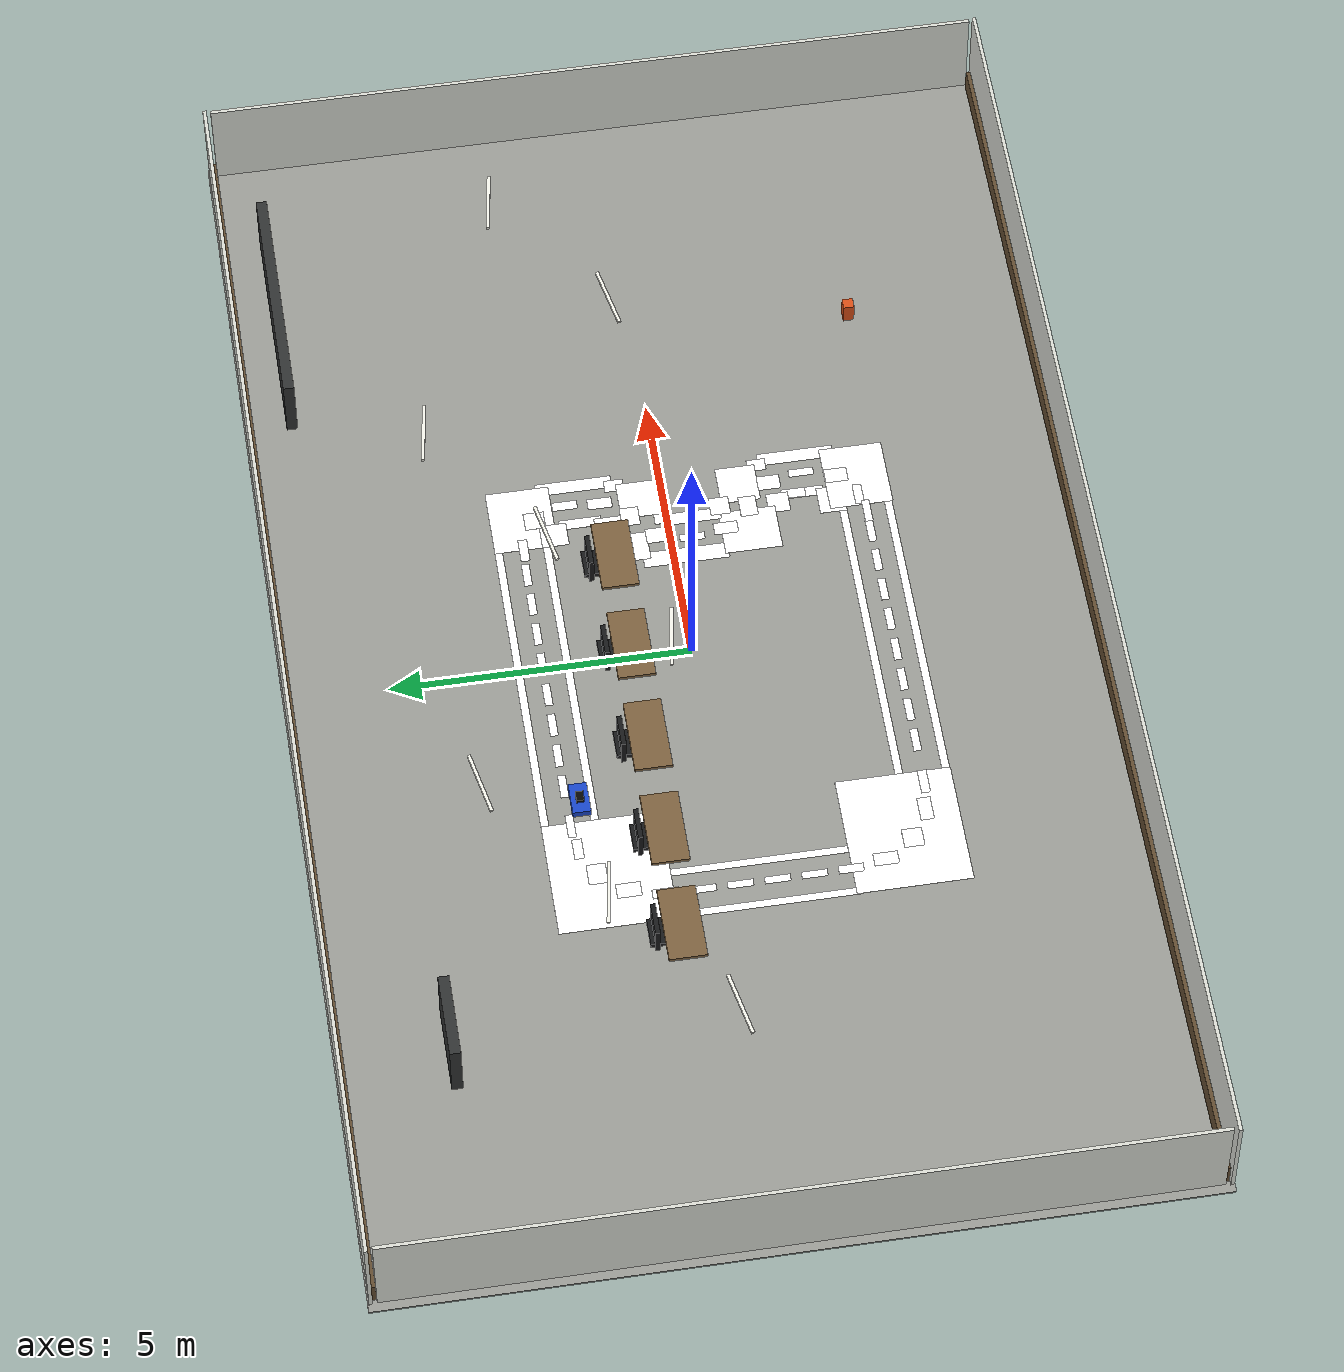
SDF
<?xml version="1.0"?>
<sdf version="1.7">
  <world name="kookmin_xycar_track">
    <gravity>0 0 -9.8</gravity>
    <magnetic_field>6e-6 2.3e-5 -4.2e-5</magnetic_field>
    <atmosphere type="adiabatic"/>
    <physics name="default_physics" default="1" type="ignored">
      <max_step_size>0.001</max_step_size>
      <real_time_factor>1</real_time_factor>
      <real_time_update_rate>1000</real_time_update_rate>
    </physics>
    <plugin filename="gz-sim-physics-system" name="gz::sim::systems::Physics"/>
    <plugin filename="gz-sim-user-commands-system" name="gz::sim::systems::UserCommands"/>
    <plugin filename="gz-sim-scene-broadcaster-system" name="gz::sim::systems::SceneBroadcaster"/>
    <plugin filename="gz-sim-sensors-system" name="gz::sim::systems::Sensors">
      <render_engine>ogre2</render_engine>
    </plugin>

    <scene>
      <ambient>0.75 0.75 0.75 1</ambient>
      <background>0.82 0.84 0.86 1</background>
      <shadows>false</shadows>
    </scene>
    <light name="sun" type="directional">
      <cast_shadows>false</cast_shadows>
      <pose>0 0 10 0 0 0</pose>
      <diffuse>0.82 0.82 0.82 1</diffuse>
      <specular>0.2 0.2 0.2 1</specular>
      <direction>-0.45 0.20 -0.88</direction>
    </light>

    <model name="kookmin_track">
      <static>true</static>
      <pose>0 0 0 0 0 0</pose>

      <link name="floor_base">
        <pose>0.0000 0.0000 -0.0150 0.000000 0.000000 0.000000</pose>
        <collision name="collision">
          <geometry><box><size>22.5000 13.5000 0.0300</size></box></geometry>
          <surface>
            <friction>
              <ode><mu>50</mu><mu2>50</mu2></ode>
              <bullet><friction>1</friction><rolling_friction>0.1</rolling_friction></bullet>
            </friction>
          </surface>
        </collision>
        <visual name="visual">
          <geometry><box><size>22.5000 13.5000 0.0300</size></box></geometry>
          <material><ambient>0.6118 0.6157 0.5922 1</ambient><diffuse>0.6118 0.6157 0.5922 1</diffuse></material>
        </visual>
      </link>
      <link name="track_texture_surface">
        <pose>0 0 0.006 0 0 0</pose>
        <visual name="visual">
          <geometry><plane><normal>0 0 1</normal><size>22.5000 13.5000</size></plane></geometry>
          <material>
            <ambient>1 1 1 1</ambient>
            <diffuse>1 1 1 1</diffuse>
            <pbr><metal><albedo_map>file://media/materials/textures/kookmin_track_road.png</albedo_map><roughness>1</roughness><metalness>0</metalness></metal></pbr>
          </material>
        </visual>
      </link>
    </model>

    <model name="white_line_cad_01">
      <static>true</static>
      <pose>-4.9850 -0.4400 0.0140 0 0 0</pose>
      <link name="white_line_cad_01_surface">
        <visual name="visual">
          <cast_shadows>false</cast_shadows>
          <geometry><plane><normal>0 0 1</normal><size>0.1300 3.1200</size></plane></geometry>
          <material>
            <ambient>1 1 1 1</ambient>
            <diffuse>1 1 1 1</diffuse>
            <emissive>0.9490 0.9490 0.9255 1</emissive>
            <pbr><metal><albedo_map>file://media/materials/textures/kookmin_white_line_cad_01.png</albedo_map><roughness>1</roughness><metalness>0</metalness></metal></pbr>
          </material>
        </visual>
      </link>
    </model>
    <model name="white_line_cad_02">
      <static>true</static>
      <pose>-4.1850 -0.4400 0.0142 0 0 0</pose>
      <link name="white_line_cad_02_surface">
        <visual name="visual">
          <cast_shadows>false</cast_shadows>
          <geometry><plane><normal>0 0 1</normal><size>0.1300 3.1200</size></plane></geometry>
          <material>
            <ambient>1 1 1 1</ambient>
            <diffuse>1 1 1 1</diffuse>
            <emissive>0.9490 0.9490 0.9255 1</emissive>
            <pbr><metal><albedo_map>file://media/materials/textures/kookmin_white_line_cad_02.png</albedo_map><roughness>1</roughness><metalness>0</metalness></metal></pbr>
          </material>
        </visual>
      </link>
    </model>
    <model name="white_line_cad_03">
      <static>true</static>
      <pose>-0.3500 -3.7050 0.0144 0 0 0</pose>
      <link name="white_line_cad_03_surface">
        <visual name="visual">
          <cast_shadows>false</cast_shadows>
          <geometry><plane><normal>0 0 1</normal><size>5.7400 0.1300</size></plane></geometry>
          <material>
            <ambient>1 1 1 1</ambient>
            <diffuse>1 1 1 1</diffuse>
            <emissive>0.9490 0.9490 0.9255 1</emissive>
            <pbr><metal><albedo_map>file://media/materials/textures/kookmin_white_line_cad_03.png</albedo_map><roughness>1</roughness><metalness>0</metalness></metal></pbr>
          </material>
        </visual>
      </link>
    </model>
    <model name="white_line_cad_04">
      <static>true</static>
      <pose>-0.3500 -2.9350 0.0146 0 0 0</pose>
      <link name="white_line_cad_04_surface">
        <visual name="visual">
          <cast_shadows>false</cast_shadows>
          <geometry><plane><normal>0 0 1</normal><size>5.7400 0.1300</size></plane></geometry>
          <material>
            <ambient>1 1 1 1</ambient>
            <diffuse>1 1 1 1</diffuse>
            <emissive>0.9490 0.9490 0.9255 1</emissive>
            <pbr><metal><albedo_map>file://media/materials/textures/kookmin_white_line_cad_04.png</albedo_map><roughness>1</roughness><metalness>0</metalness></metal></pbr>
          </material>
        </visual>
      </link>
    </model>
    <model name="white_line_cad_05">
      <static>true</static>
      <pose>-0.3500 2.0550 0.0148 0 0 0</pose>
      <link name="white_line_cad_05_surface">
        <visual name="visual">
          <cast_shadows>false</cast_shadows>
          <geometry><plane><normal>0 0 1</normal><size>5.7800 0.1300</size></plane></geometry>
          <material>
            <ambient>1 1 1 1</ambient>
            <diffuse>1 1 1 1</diffuse>
            <emissive>0.9490 0.9490 0.9255 1</emissive>
            <pbr><metal><albedo_map>file://media/materials/textures/kookmin_white_line_cad_05.png</albedo_map><roughness>1</roughness><metalness>0</metalness></metal></pbr>
          </material>
        </visual>
      </link>
    </model>
    <model name="white_line_cad_06">
      <static>true</static>
      <pose>-0.3500 2.8650 0.0150 0 0 0</pose>
      <link name="white_line_cad_06_surface">
        <visual name="visual">
          <cast_shadows>false</cast_shadows>
          <geometry><plane><normal>0 0 1</normal><size>5.7800 0.1300</size></plane></geometry>
          <material>
            <ambient>1 1 1 1</ambient>
            <diffuse>1 1 1 1</diffuse>
            <emissive>0.9490 0.9490 0.9255 1</emissive>
            <pbr><metal><albedo_map>file://media/materials/textures/kookmin_white_line_cad_06.png</albedo_map><roughness>1</roughness><metalness>0</metalness></metal></pbr>
          </material>
        </visual>
      </link>
    </model>
    <model name="white_line_cad_07">
      <static>true</static>
      <pose>2.8650 -2.3150 0.0152 0 0 0</pose>
      <link name="white_line_cad_07_surface">
        <visual name="visual">
          <cast_shadows>false</cast_shadows>
          <geometry><plane><normal>0 0 1</normal><size>0.1900 0.7100</size></plane></geometry>
          <material>
            <ambient>1 1 1 1</ambient>
            <diffuse>1 1 1 1</diffuse>
            <emissive>0.9490 0.9490 0.9255 1</emissive>
            <pbr><metal><albedo_map>file://media/materials/textures/kookmin_white_line_cad_07.png</albedo_map><roughness>1</roughness><metalness>0</metalness></metal></pbr>
          </material>
        </visual>
      </link>
    </model>
    <model name="white_line_cad_08">
      <static>true</static>
      <pose>2.6450 -2.7750 0.0154 0 0 0</pose>
      <link name="white_line_cad_08_surface">
        <visual name="visual">
          <cast_shadows>false</cast_shadows>
          <geometry><plane><normal>0 0 1</normal><size>0.5100 0.4500</size></plane></geometry>
          <material>
            <ambient>1 1 1 1</ambient>
            <diffuse>1 1 1 1</diffuse>
            <emissive>0.9490 0.9490 0.9255 1</emissive>
            <pbr><metal><albedo_map>file://media/materials/textures/kookmin_white_line_cad_08.png</albedo_map><roughness>1</roughness><metalness>0</metalness></metal></pbr>
          </material>
        </visual>
      </link>
    </model>
    <model name="white_line_cad_09">
      <static>true</static>
      <pose>3.0700 -3.2600 0.0156 0 0 0</pose>
      <link name="white_line_cad_09_surface">
        <visual name="visual">
          <cast_shadows>false</cast_shadows>
          <geometry><plane><normal>0 0 1</normal><size>1.2200 1.0600</size></plane></geometry>
          <material>
            <ambient>1 1 1 1</ambient>
            <diffuse>1 1 1 1</diffuse>
            <emissive>0.9490 0.9490 0.9255 1</emissive>
            <pbr><metal><albedo_map>file://media/materials/textures/kookmin_white_line_cad_09.png</albedo_map><roughness>1</roughness><metalness>0</metalness></metal></pbr>
          </material>
        </visual>
      </link>
    </model>
    <model name="white_line_cad_10">
      <static>true</static>
      <pose>3.6300 -2.3200 0.0158 0 0 0</pose>
      <link name="white_line_cad_10_surface">
        <visual name="visual">
          <cast_shadows>false</cast_shadows>
          <geometry><plane><normal>0 0 1</normal><size>0.2400 1.2800</size></plane></geometry>
          <material>
            <ambient>1 1 1 1</ambient>
            <diffuse>1 1 1 1</diffuse>
            <emissive>0.9490 0.9490 0.9255 1</emissive>
            <pbr><metal><albedo_map>file://media/materials/textures/kookmin_white_line_cad_10.png</albedo_map><roughness>1</roughness><metalness>0</metalness></metal></pbr>
          </material>
        </visual>
      </link>
    </model>
    <model name="white_line_cad_11">
      <static>true</static>
      <pose>3.5350 -1.6450 0.0160 0 0 0</pose>
      <link name="white_line_cad_11_surface">
        <visual name="visual">
          <cast_shadows>false</cast_shadows>
          <geometry><plane><normal>0 0 1</normal><size>0.2300 0.3100</size></plane></geometry>
          <material>
            <ambient>1 1 1 1</ambient>
            <diffuse>1 1 1 1</diffuse>
            <emissive>0.9490 0.9490 0.9255 1</emissive>
            <pbr><metal><albedo_map>file://media/materials/textures/kookmin_white_line_cad_11.png</albedo_map><roughness>1</roughness><metalness>0</metalness></metal></pbr>
          </material>
        </visual>
      </link>
    </model>
    <model name="white_line_cad_12">
      <static>true</static>
      <pose>2.8150 1.4450 0.0162 0 0 0</pose>
      <link name="white_line_cad_12_surface">
        <visual name="visual">
          <cast_shadows>false</cast_shadows>
          <geometry><plane><normal>0 0 1</normal><size>0.1900 0.7100</size></plane></geometry>
          <material>
            <ambient>1 1 1 1</ambient>
            <diffuse>1 1 1 1</diffuse>
            <emissive>0.9490 0.9490 0.9255 1</emissive>
            <pbr><metal><albedo_map>file://media/materials/textures/kookmin_white_line_cad_12.png</albedo_map><roughness>1</roughness><metalness>0</metalness></metal></pbr>
          </material>
        </visual>
      </link>
    </model>
    <model name="white_line_cad_13">
      <static>true</static>
      <pose>2.6000 0.9750 0.0164 0 0 0</pose>
      <link name="white_line_cad_13_surface">
        <visual name="visual">
          <cast_shadows>false</cast_shadows>
          <geometry><plane><normal>0 0 1</normal><size>0.5200 0.4700</size></plane></geometry>
          <material>
            <ambient>1 1 1 1</ambient>
            <diffuse>1 1 1 1</diffuse>
            <emissive>0.9490 0.9490 0.9255 1</emissive>
            <pbr><metal><albedo_map>file://media/materials/textures/kookmin_white_line_cad_13.png</albedo_map><roughness>1</roughness><metalness>0</metalness></metal></pbr>
          </material>
        </visual>
      </link>
    </model>
    <model name="white_line_cad_14">
      <static>true</static>
      <pose>3.0200 2.4000 0.0166 0 0 0</pose>
      <link name="white_line_cad_14_surface">
        <visual name="visual">
          <cast_shadows>false</cast_shadows>
          <geometry><plane><normal>0 0 1</normal><size>1.2200 1.0600</size></plane></geometry>
          <material>
            <ambient>1 1 1 1</ambient>
            <diffuse>1 1 1 1</diffuse>
            <emissive>0.9490 0.9490 0.9255 1</emissive>
            <pbr><metal><albedo_map>file://media/materials/textures/kookmin_white_line_cad_14.png</albedo_map><roughness>1</roughness><metalness>0</metalness></metal></pbr>
          </material>
        </visual>
      </link>
    </model>
    <model name="white_line_cad_15">
      <static>true</static>
      <pose>3.5800 1.4500 0.0168 0 0 0</pose>
      <link name="white_line_cad_15_surface">
        <visual name="visual">
          <cast_shadows>false</cast_shadows>
          <geometry><plane><normal>0 0 1</normal><size>0.2400 1.2800</size></plane></geometry>
          <material>
            <ambient>1 1 1 1</ambient>
            <diffuse>1 1 1 1</diffuse>
            <emissive>0.9490 0.9490 0.9255 1</emissive>
            <pbr><metal><albedo_map>file://media/materials/textures/kookmin_white_line_cad_15.png</albedo_map><roughness>1</roughness><metalness>0</metalness></metal></pbr>
          </material>
        </visual>
      </link>
    </model>
    <model name="white_line_cad_16">
      <static>true</static>
      <pose>3.4850 0.7800 0.0170 0 0 0</pose>
      <link name="white_line_cad_16_surface">
        <visual name="visual">
          <cast_shadows>false</cast_shadows>
          <geometry><plane><normal>0 0 1</normal><size>0.2300 0.3200</size></plane></geometry>
          <material>
            <ambient>1 1 1 1</ambient>
            <diffuse>1 1 1 1</diffuse>
            <emissive>0.9490 0.9490 0.9255 1</emissive>
            <pbr><metal><albedo_map>file://media/materials/textures/kookmin_white_line_cad_16.png</albedo_map><roughness>1</roughness><metalness>0</metalness></metal></pbr>
          </material>
        </visual>
      </link>
    </model>
    <model name="white_line_cad_17">
      <static>true</static>
      <pose>1.9000 -0.2050 0.0172 0 0 0</pose>
      <link name="white_line_cad_17_surface">
        <visual name="visual">
          <cast_shadows>false</cast_shadows>
          <geometry><plane><normal>0 0 1</normal><size>0.3000 1.4300</size></plane></geometry>
          <material>
            <ambient>1 1 1 1</ambient>
            <diffuse>1 1 1 1</diffuse>
            <emissive>0.9490 0.9490 0.9255 1</emissive>
            <pbr><metal><albedo_map>file://media/materials/textures/kookmin_white_line_cad_17.png</albedo_map><roughness>1</roughness><metalness>0</metalness></metal></pbr>
          </material>
        </visual>
      </link>
    </model>
    <model name="white_line_cad_18">
      <static>true</static>
      <pose>-3.6800 1.5650 0.0174 0 0 0</pose>
      <link name="white_line_cad_18_surface">
        <visual name="visual">
          <cast_shadows>false</cast_shadows>
          <geometry><plane><normal>0 0 1</normal><size>1.1400 1.1300</size></plane></geometry>
          <material>
            <ambient>1 1 1 1</ambient>
            <diffuse>1 1 1 1</diffuse>
            <emissive>0.9490 0.9490 0.9255 1</emissive>
            <pbr><metal><albedo_map>file://media/materials/textures/kookmin_white_line_cad_18.png</albedo_map><roughness>1</roughness><metalness>0</metalness></metal></pbr>
          </material>
        </visual>
      </link>
    </model>
    <model name="white_line_cad_19">
      <static>true</static>
      <pose>-4.0300 1.9650 0.0176 0 0 0</pose>
      <link name="white_line_cad_19_surface">
        <visual name="visual">
          <cast_shadows>false</cast_shadows>
          <geometry><plane><normal>0 0 1</normal><size>2.0400 1.9300</size></plane></geometry>
          <material>
            <ambient>1 1 1 1</ambient>
            <diffuse>1 1 1 1</diffuse>
            <emissive>0.9490 0.9490 0.9255 1</emissive>
            <pbr><metal><albedo_map>file://media/materials/textures/kookmin_white_line_cad_19.png</albedo_map><roughness>1</roughness><metalness>0</metalness></metal></pbr>
          </material>
        </visual>
      </link>
    </model>
    <model name="white_line_cad_20">
      <static>true</static>
      <pose>-3.6750 -2.4450 0.0178 0 0 0</pose>
      <link name="white_line_cad_20_surface">
        <visual name="visual">
          <cast_shadows>false</cast_shadows>
          <geometry><plane><normal>0 0 1</normal><size>1.1700 1.1300</size></plane></geometry>
          <material>
            <ambient>1 1 1 1</ambient>
            <diffuse>1 1 1 1</diffuse>
            <emissive>0.9490 0.9490 0.9255 1</emissive>
            <pbr><metal><albedo_map>file://media/materials/textures/kookmin_white_line_cad_20.png</albedo_map><roughness>1</roughness><metalness>0</metalness></metal></pbr>
          </material>
        </visual>
      </link>
    </model>
    <model name="white_line_cad_21">
      <static>true</static>
      <pose>-3.9700 -2.8300 0.0180 0 0 0</pose>
      <link name="white_line_cad_21_surface">
        <visual name="visual">
          <cast_shadows>false</cast_shadows>
          <geometry><plane><normal>0 0 1</normal><size>2.1400 1.9000</size></plane></geometry>
          <material>
            <ambient>1 1 1 1</ambient>
            <diffuse>1 1 1 1</diffuse>
            <emissive>0.9490 0.9490 0.9255 1</emissive>
            <pbr><metal><albedo_map>file://media/materials/textures/kookmin_white_line_cad_21.png</albedo_map><roughness>1</roughness><metalness>0</metalness></metal></pbr>
          </material>
        </visual>
      </link>
    </model>
    <model name="white_line_cad_22">
      <static>true</static>
      <pose>2.8700 -2.1650 0.0182 0 0 0</pose>
      <link name="white_line_cad_22_surface">
        <visual name="visual">
          <cast_shadows>false</cast_shadows>
          <geometry><plane><normal>0 0 1</normal><size>0.1800 0.4100</size></plane></geometry>
          <material>
            <ambient>1 1 1 1</ambient>
            <diffuse>1 1 1 1</diffuse>
            <emissive>0.9490 0.9490 0.9255 1</emissive>
            <pbr><metal><albedo_map>file://media/materials/textures/kookmin_white_line_cad_22.png</albedo_map><roughness>1</roughness><metalness>0</metalness></metal></pbr>
          </material>
        </visual>
      </link>
    </model>
    <model name="white_line_cad_23">
      <static>true</static>
      <pose>2.2450 -1.3400 0.0184 0 0 0</pose>
      <link name="white_line_cad_23_surface">
        <visual name="visual">
          <cast_shadows>false</cast_shadows>
          <geometry><plane><normal>0 0 1</normal><size>0.8300 0.9600</size></plane></geometry>
          <material>
            <ambient>1 1 1 1</ambient>
            <diffuse>1 1 1 1</diffuse>
            <emissive>0.9490 0.9490 0.9255 1</emissive>
            <pbr><metal><albedo_map>file://media/materials/textures/kookmin_white_line_cad_23.png</albedo_map><roughness>1</roughness><metalness>0</metalness></metal></pbr>
          </material>
        </visual>
      </link>
    </model>
    <model name="white_line_cad_24">
      <static>true</static>
      <pose>2.7200 -1.8850 0.0186 0 0 0</pose>
      <link name="white_line_cad_24_surface">
        <visual name="visual">
          <cast_shadows>false</cast_shadows>
          <geometry><plane><normal>0 0 1</normal><size>0.3800 0.3700</size></plane></geometry>
          <material>
            <ambient>1 1 1 1</ambient>
            <diffuse>1 1 1 1</diffuse>
            <emissive>0.9490 0.9490 0.9255 1</emissive>
            <pbr><metal><albedo_map>file://media/materials/textures/kookmin_white_line_cad_24.png</albedo_map><roughness>1</roughness><metalness>0</metalness></metal></pbr>
          </material>
        </visual>
      </link>
    </model>
    <model name="white_line_cad_25">
      <static>true</static>
      <pose>2.1950 0.6250 0.0188 0 0 0</pose>
      <link name="white_line_cad_25_surface">
        <visual name="visual">
          <cast_shadows>false</cast_shadows>
          <geometry><plane><normal>0 0 1</normal><size>0.5500 0.4900</size></plane></geometry>
          <material>
            <ambient>1 1 1 1</ambient>
            <diffuse>1 1 1 1</diffuse>
            <emissive>0.9490 0.9490 0.9255 1</emissive>
            <pbr><metal><albedo_map>file://media/materials/textures/kookmin_white_line_cad_25.png</albedo_map><roughness>1</roughness><metalness>0</metalness></metal></pbr>
          </material>
        </visual>
      </link>
    </model>
    <model name="white_line_cad_26">
      <static>true</static>
      <pose>2.7550 0.0650 0.0190 0 0 0</pose>
      <link name="white_line_cad_26_surface">
        <visual name="visual">
          <cast_shadows>false</cast_shadows>
          <geometry><plane><normal>0 0 1</normal><size>0.3300 0.2900</size></plane></geometry>
          <material>
            <ambient>1 1 1 1</ambient>
            <diffuse>1 1 1 1</diffuse>
            <emissive>0.9490 0.9490 0.9255 1</emissive>
            <pbr><metal><albedo_map>file://media/materials/textures/kookmin_white_line_cad_26.png</albedo_map><roughness>1</roughness><metalness>0</metalness></metal></pbr>
          </material>
        </visual>
      </link>
    </model>
    <model name="white_line_cad_27">
      <static>true</static>
      <pose>3.1450 0.4150 0.0192 0 0 0</pose>
      <link name="white_line_cad_27_surface">
        <visual name="visual">
          <cast_shadows>false</cast_shadows>
          <geometry><plane><normal>0 0 1</normal><size>0.7100 0.6700</size></plane></geometry>
          <material>
            <ambient>1 1 1 1</ambient>
            <diffuse>1 1 1 1</diffuse>
            <emissive>0.9490 0.9490 0.9255 1</emissive>
            <pbr><metal><albedo_map>file://media/materials/textures/kookmin_white_line_cad_27.png</albedo_map><roughness>1</roughness><metalness>0</metalness></metal></pbr>
          </material>
        </visual>
      </link>
    </model>
    <model name="white_line_cad_28">
      <static>true</static>
      <pose>2.6550 -0.4300 0.0194 0 0 0</pose>
      <link name="white_line_cad_28_surface">
        <visual name="visual">
          <cast_shadows>false</cast_shadows>
          <geometry><plane><normal>0 0 1</normal><size>0.2300 0.9400</size></plane></geometry>
          <material>
            <ambient>1 1 1 1</ambient>
            <diffuse>1 1 1 1</diffuse>
            <emissive>0.9490 0.9490 0.9255 1</emissive>
            <pbr><metal><albedo_map>file://media/materials/textures/kookmin_white_line_cad_28.png</albedo_map><roughness>1</roughness><metalness>0</metalness></metal></pbr>
          </material>
        </visual>
      </link>
    </model>
    <model name="white_line_cad_29">
      <static>true</static>
      <pose>3.1950 -1.2750 0.0196 0 0 0</pose>
      <link name="white_line_cad_29_surface">
        <visual name="visual">
          <cast_shadows>false</cast_shadows>
          <geometry><plane><normal>0 0 1</normal><size>0.7100 0.6700</size></plane></geometry>
          <material>
            <ambient>1 1 1 1</ambient>
            <diffuse>1 1 1 1</diffuse>
            <emissive>0.9490 0.9490 0.9255 1</emissive>
            <pbr><metal><albedo_map>file://media/materials/textures/kookmin_white_line_cad_29.png</albedo_map><roughness>1</roughness><metalness>0</metalness></metal></pbr>
          </material>
        </visual>
      </link>
    </model>
    <model name="white_line_cad_30">
      <static>true</static>
      <pose>2.8000 -0.9050 0.0198 0 0 0</pose>
      <link name="white_line_cad_30_surface">
        <visual name="visual">
          <cast_shadows>false</cast_shadows>
          <geometry><plane><normal>0 0 1</normal><size>0.3400 0.3300</size></plane></geometry>
          <material>
            <ambient>1 1 1 1</ambient>
            <diffuse>1 1 1 1</diffuse>
            <emissive>0.9490 0.9490 0.9255 1</emissive>
            <pbr><metal><albedo_map>file://media/materials/textures/kookmin_white_line_cad_30.png</albedo_map><roughness>1</roughness><metalness>0</metalness></metal></pbr>
          </material>
        </visual>
      </link>
    </model>
    <model name="white_line_cad_31">
      <static>true</static>
      <pose>2.6300 1.9050 0.0200 0 0 0</pose>
      <link name="white_line_cad_31_surface">
        <visual name="visual">
          <cast_shadows>false</cast_shadows>
          <geometry><plane><normal>0 0 1</normal><size>0.4400 0.4500</size></plane></geometry>
          <material>
            <ambient>1 1 1 1</ambient>
            <diffuse>1 1 1 1</diffuse>
            <emissive>0.9490 0.9490 0.9255 1</emissive>
            <pbr><metal><albedo_map>file://media/materials/textures/kookmin_white_line_cad_31.png</albedo_map><roughness>1</roughness><metalness>0</metalness></metal></pbr>
          </material>
        </visual>
      </link>
    </model>

    <model name="yellow_centerline_dash_001">
      <static>true</static>
      <pose>-2.3050 2.4650 0.0265 0 0 0</pose>
      <link name="yellow_centerline_dash_001_surface">
        <visual name="visual">
          <cast_shadows>false</cast_shadows>
          <geometry><plane><normal>0 0 1</normal><size>0.4300 0.1300</size></plane></geometry>
          <material>
            <ambient>1 1 1 1</ambient>
            <diffuse>1 1 1 1</diffuse>
            <emissive>1.0000 0.7686 0.0471 1</emissive>
            <pbr><metal><albedo_map>file://media/materials/textures/kookmin_yellow_centerline_dash_001.png</albedo_map><roughness>1</roughness><metalness>0</metalness></metal></pbr>
          </material>
        </visual>
      </link>
    </model>
    <model name="yellow_centerline_dash_002">
      <static>true</static>
      <pose>-1.7050 2.4650 0.0267 0 0 0</pose>
      <link name="yellow_centerline_dash_002_surface">
        <visual name="visual">
          <cast_shadows>false</cast_shadows>
          <geometry><plane><normal>0 0 1</normal><size>0.4300 0.1300</size></plane></geometry>
          <material>
            <ambient>1 1 1 1</ambient>
            <diffuse>1 1 1 1</diffuse>
            <emissive>1.0000 0.7686 0.0471 1</emissive>
            <pbr><metal><albedo_map>file://media/materials/textures/kookmin_yellow_centerline_dash_002.png</albedo_map><roughness>1</roughness><metalness>0</metalness></metal></pbr>
          </material>
        </visual>
      </link>
    </model>
    <model name="yellow_centerline_dash_003">
      <static>true</static>
      <pose>-1.1050 2.4650 0.0269 0 0 0</pose>
      <link name="yellow_centerline_dash_003_surface">
        <visual name="visual">
          <cast_shadows>false</cast_shadows>
          <geometry><plane><normal>0 0 1</normal><size>0.4300 0.1300</size></plane></geometry>
          <material>
            <ambient>1 1 1 1</ambient>
            <diffuse>1 1 1 1</diffuse>
            <emissive>1.0000 0.7686 0.0471 1</emissive>
            <pbr><metal><albedo_map>file://media/materials/textures/kookmin_yellow_centerline_dash_003.png</albedo_map><roughness>1</roughness><metalness>0</metalness></metal></pbr>
          </material>
        </visual>
      </link>
    </model>
    <model name="yellow_centerline_dash_004">
      <static>true</static>
      <pose>-0.5050 2.4650 0.0271 0 0 0</pose>
      <link name="yellow_centerline_dash_004_surface">
        <visual name="visual">
          <cast_shadows>false</cast_shadows>
          <geometry><plane><normal>0 0 1</normal><size>0.4300 0.1300</size></plane></geometry>
          <material>
            <ambient>1 1 1 1</ambient>
            <diffuse>1 1 1 1</diffuse>
            <emissive>1.0000 0.7686 0.0471 1</emissive>
            <pbr><metal><albedo_map>file://media/materials/textures/kookmin_yellow_centerline_dash_004.png</albedo_map><roughness>1</roughness><metalness>0</metalness></metal></pbr>
          </material>
        </visual>
      </link>
    </model>
    <model name="yellow_centerline_dash_005">
      <static>true</static>
      <pose>0.1050 2.4650 0.0273 0 0 0</pose>
      <link name="yellow_centerline_dash_005_surface">
        <visual name="visual">
          <cast_shadows>false</cast_shadows>
          <geometry><plane><normal>0 0 1</normal><size>0.4300 0.1300</size></plane></geometry>
          <material>
            <ambient>1 1 1 1</ambient>
            <diffuse>1 1 1 1</diffuse>
            <emissive>1.0000 0.7686 0.0471 1</emissive>
            <pbr><metal><albedo_map>file://media/materials/textures/kookmin_yellow_centerline_dash_005.png</albedo_map><roughness>1</roughness><metalness>0</metalness></metal></pbr>
          </material>
        </visual>
      </link>
    </model>
    <model name="yellow_centerline_dash_006">
      <static>true</static>
      <pose>0.7050 2.4650 0.0275 0 0 0</pose>
      <link name="yellow_centerline_dash_006_surface">
        <visual name="visual">
          <cast_shadows>false</cast_shadows>
          <geometry><plane><normal>0 0 1</normal><size>0.4300 0.1300</size></plane></geometry>
          <material>
            <ambient>1 1 1 1</ambient>
            <diffuse>1 1 1 1</diffuse>
            <emissive>1.0000 0.7686 0.0471 1</emissive>
            <pbr><metal><albedo_map>file://media/materials/textures/kookmin_yellow_centerline_dash_006.png</albedo_map><roughness>1</roughness><metalness>0</metalness></metal></pbr>
          </material>
        </visual>
      </link>
    </model>
    <model name="yellow_centerline_dash_007">
      <static>true</static>
      <pose>1.3050 2.4650 0.0277 0 0 0</pose>
      <link name="yellow_centerline_dash_007_surface">
        <visual name="visual">
          <cast_shadows>false</cast_shadows>
          <geometry><plane><normal>0 0 1</normal><size>0.4300 0.1300</size></plane></geometry>
          <material>
            <ambient>1 1 1 1</ambient>
            <diffuse>1 1 1 1</diffuse>
            <emissive>1.0000 0.7686 0.0471 1</emissive>
            <pbr><metal><albedo_map>file://media/materials/textures/kookmin_yellow_centerline_dash_007.png</albedo_map><roughness>1</roughness><metalness>0</metalness></metal></pbr>
          </material>
        </visual>
      </link>
    </model>
    <model name="yellow_centerline_dash_008">
      <static>true</static>
      <pose>1.9000 2.4650 0.0279 0 0 0</pose>
      <link name="yellow_centerline_dash_008_surface">
        <visual name="visual">
          <cast_shadows>false</cast_shadows>
          <geometry><plane><normal>0 0 1</normal><size>0.4400 0.1300</size></plane></geometry>
          <material>
            <ambient>1 1 1 1</ambient>
            <diffuse>1 1 1 1</diffuse>
            <emissive>1.0000 0.7686 0.0471 1</emissive>
            <pbr><metal><albedo_map>file://media/materials/textures/kookmin_yellow_centerline_dash_008.png</albedo_map><roughness>1</roughness><metalness>0</metalness></metal></pbr>
          </material>
        </visual>
      </link>
    </model>
    <model name="yellow_centerline_dash_009">
      <static>true</static>
      <pose>-3.0750 2.4550 0.0281 0 0 0</pose>
      <link name="yellow_centerline_dash_009_surface">
        <visual name="visual">
          <cast_shadows>false</cast_shadows>
          <geometry><plane><normal>0 0 1</normal><size>0.4300 0.1300</size></plane></geometry>
          <material>
            <ambient>1 1 1 1</ambient>
            <diffuse>1 1 1 1</diffuse>
            <emissive>1.0000 0.7686 0.0471 1</emissive>
            <pbr><metal><albedo_map>file://media/materials/textures/kookmin_yellow_centerline_dash_009.png</albedo_map><roughness>1</roughness><metalness>0</metalness></metal></pbr>
          </material>
        </visual>
      </link>
    </model>
    <model name="yellow_centerline_dash_010">
      <static>true</static>
      <pose>2.3950 2.4450 0.0283 0 0 0</pose>
      <link name="yellow_centerline_dash_010_surface">
        <visual name="visual">
          <cast_shadows>false</cast_shadows>
          <geometry><plane><normal>0 0 1</normal><size>0.4300 0.1500</size></plane></geometry>
          <material>
            <ambient>1 1 1 1</ambient>
            <diffuse>1 1 1 1</diffuse>
            <emissive>1.0000 0.7686 0.0471 1</emissive>
            <pbr><metal><albedo_map>file://media/materials/textures/kookmin_yellow_centerline_dash_010.png</albedo_map><roughness>1</roughness><metalness>0</metalness></metal></pbr>
          </material>
        </visual>
      </link>
    </model>
    <model name="yellow_centerline_dash_011">
      <static>true</static>
      <pose>-3.5250 2.4000 0.0285 0 0 0</pose>
      <link name="yellow_centerline_dash_011_surface">
        <visual name="visual">
          <cast_shadows>false</cast_shadows>
          <geometry><plane><normal>0 0 1</normal><size>0.3700 0.1600</size></plane></geometry>
          <material>
            <ambient>1 1 1 1</ambient>
            <diffuse>1 1 1 1</diffuse>
            <emissive>1.0000 0.7686 0.0471 1</emissive>
            <pbr><metal><albedo_map>file://media/materials/textures/kookmin_yellow_centerline_dash_011.png</albedo_map><roughness>1</roughness><metalness>0</metalness></metal></pbr>
          </material>
        </visual>
      </link>
    </model>
    <model name="yellow_centerline_dash_012">
      <static>true</static>
      <pose>2.9650 2.1900 0.0287 0 0 0</pose>
      <link name="yellow_centerline_dash_012_surface">
        <visual name="visual">
          <cast_shadows>false</cast_shadows>
          <geometry><plane><normal>0 0 1</normal><size>0.3300 0.3400</size></plane></geometry>
          <material>
            <ambient>1 1 1 1</ambient>
            <diffuse>1 1 1 1</diffuse>
            <emissive>1.0000 0.7686 0.0471 1</emissive>
            <pbr><metal><albedo_map>file://media/materials/textures/kookmin_yellow_centerline_dash_012.png</albedo_map><roughness>1</roughness><metalness>0</metalness></metal></pbr>
          </material>
        </visual>
      </link>
    </model>
    <model name="yellow_centerline_dash_013">
      <static>true</static>
      <pose>-4.0350 2.1650 0.0289 0 0 0</pose>
      <link name="yellow_centerline_dash_013_surface">
        <visual name="visual">
          <cast_shadows>false</cast_shadows>
          <geometry><plane><normal>0 0 1</normal><size>0.3700 0.3100</size></plane></geometry>
          <material>
            <ambient>1 1 1 1</ambient>
            <diffuse>1 1 1 1</diffuse>
            <emissive>1.0000 0.7686 0.0471 1</emissive>
            <pbr><metal><albedo_map>file://media/materials/textures/kookmin_yellow_centerline_dash_013.png</albedo_map><roughness>1</roughness><metalness>0</metalness></metal></pbr>
          </material>
        </visual>
      </link>
    </model>
    <model name="yellow_centerline_dash_014">
      <static>true</static>
      <pose>-4.4100 1.7100 0.0291 0 0 0</pose>
      <link name="yellow_centerline_dash_014_surface">
        <visual name="visual">
          <cast_shadows>false</cast_shadows>
          <geometry><plane><normal>0 0 1</normal><size>0.2600 0.4000</size></plane></geometry>
          <material>
            <ambient>1 1 1 1</ambient>
            <diffuse>1 1 1 1</diffuse>
            <emissive>1.0000 0.7686 0.0471 1</emissive>
            <pbr><metal><albedo_map>file://media/materials/textures/kookmin_yellow_centerline_dash_014.png</albedo_map><roughness>1</roughness><metalness>0</metalness></metal></pbr>
          </material>
        </visual>
      </link>
    </model>
    <model name="yellow_centerline_dash_015">
      <static>true</static>
      <pose>3.1950 1.6500 0.0293 0 0 0</pose>
      <link name="yellow_centerline_dash_015_surface">
        <visual name="visual">
          <cast_shadows>false</cast_shadows>
          <geometry><plane><normal>0 0 1</normal><size>0.1700 0.4200</size></plane></geometry>
          <material>
            <ambient>1 1 1 1</ambient>
            <diffuse>1 1 1 1</diffuse>
            <emissive>1.0000 0.7686 0.0471 1</emissive>
            <pbr><metal><albedo_map>file://media/materials/textures/kookmin_yellow_centerline_dash_015.png</albedo_map><roughness>1</roughness><metalness>0</metalness></metal></pbr>
          </material>
        </visual>
      </link>
    </model>
    <model name="yellow_centerline_dash_016">
      <static>true</static>
      <pose>-4.5550 1.1350 0.0295 0 0 0</pose>
      <link name="yellow_centerline_dash_016_surface">
        <visual name="visual">
          <cast_shadows>false</cast_shadows>
          <geometry><plane><normal>0 0 1</normal><size>0.1700 0.4300</size></plane></geometry>
          <material>
            <ambient>1 1 1 1</ambient>
            <diffuse>1 1 1 1</diffuse>
            <emissive>1.0000 0.7686 0.0471 1</emissive>
            <pbr><metal><albedo_map>file://media/materials/textures/kookmin_yellow_centerline_dash_016.png</albedo_map><roughness>1</roughness><metalness>0</metalness></metal></pbr>
          </material>
        </visual>
      </link>
    </model>
    <model name="yellow_centerline_dash_017">
      <static>true</static>
      <pose>3.1550 1.0650 0.0297 0 0 0</pose>
      <link name="yellow_centerline_dash_017_surface">
        <visual name="visual">
          <cast_shadows>false</cast_shadows>
          <geometry><plane><normal>0 0 1</normal><size>0.2100 0.4100</size></plane></geometry>
          <material>
            <ambient>1 1 1 1</ambient>
            <diffuse>1 1 1 1</diffuse>
            <emissive>1.0000 0.7686 0.0471 1</emissive>
            <pbr><metal><albedo_map>file://media/materials/textures/kookmin_yellow_centerline_dash_017.png</albedo_map><roughness>1</roughness><metalness>0</metalness></metal></pbr>
          </material>
        </visual>
      </link>
    </model>
    <model name="yellow_centerline_dash_018">
      <static>true</static>
      <pose>2.8100 0.6050 0.0299 0 0 0</pose>
      <link name="yellow_centerline_dash_018_surface">
        <visual name="visual">
          <cast_shadows>false</cast_shadows>
          <geometry><plane><normal>0 0 1</normal><size>0.3600 0.3100</size></plane></geometry>
          <material>
            <ambient>1 1 1 1</ambient>
            <diffuse>1 1 1 1</diffuse>
            <emissive>1.0000 0.7686 0.0471 1</emissive>
            <pbr><metal><albedo_map>file://media/materials/textures/kookmin_yellow_centerline_dash_018.png</albedo_map><roughness>1</roughness><metalness>0</metalness></metal></pbr>
          </material>
        </visual>
      </link>
    </model>
    <model name="yellow_centerline_dash_019">
      <static>true</static>
      <pose>-4.5750 0.5300 0.0301 0 0 0</pose>
      <link name="yellow_centerline_dash_019_surface">
        <visual name="visual">
          <cast_shadows>false</cast_shadows>
          <geometry><plane><normal>0 0 1</normal><size>0.1300 0.4200</size></plane></geometry>
          <material>
            <ambient>1 1 1 1</ambient>
            <diffuse>1 1 1 1</diffuse>
            <emissive>1.0000 0.7686 0.0471 1</emissive>
            <pbr><metal><albedo_map>file://media/materials/textures/kookmin_yellow_centerline_dash_019.png</albedo_map><roughness>1</roughness><metalness>0</metalness></metal></pbr>
          </material>
        </visual>
      </link>
    </model>
    <model name="yellow_centerline_dash_020">
      <static>true</static>
      <pose>2.3650 0.2150 0.0303 0 0 0</pose>
      <link name="yellow_centerline_dash_020_surface">
        <visual name="visual">
          <cast_shadows>false</cast_shadows>
          <geometry><plane><normal>0 0 1</normal><size>0.2900 0.3700</size></plane></geometry>
          <material>
            <ambient>1 1 1 1</ambient>
            <diffuse>1 1 1 1</diffuse>
            <emissive>1.0000 0.7686 0.0471 1</emissive>
            <pbr><metal><albedo_map>file://media/materials/textures/kookmin_yellow_centerline_dash_020.png</albedo_map><roughness>1</roughness><metalness>0</metalness></metal></pbr>
          </material>
        </visual>
      </link>
    </model>
    <model name="yellow_centerline_dash_021">
      <static>true</static>
      <pose>-4.5750 -0.0700 0.0305 0 0 0</pose>
      <link name="yellow_centerline_dash_021_surface">
        <visual name="visual">
          <cast_shadows>false</cast_shadows>
          <geometry><plane><normal>0 0 1</normal><size>0.1300 0.4200</size></plane></geometry>
          <material>
            <ambient>1 1 1 1</ambient>
            <diffuse>1 1 1 1</diffuse>
            <emissive>1.0000 0.7686 0.0471 1</emissive>
            <pbr><metal><albedo_map>file://media/materials/textures/kookmin_yellow_centerline_dash_021.png</albedo_map><roughness>1</roughness><metalness>0</metalness></metal></pbr>
          </material>
        </visual>
      </link>
    </model>
    <model name="yellow_centerline_dash_022">
      <static>true</static>
      <pose>2.2400 -0.3600 0.0307 0 0 0</pose>
      <link name="yellow_centerline_dash_022_surface">
        <visual name="visual">
          <cast_shadows>false</cast_shadows>
          <geometry><plane><normal>0 0 1</normal><size>0.1400 0.4200</size></plane></geometry>
          <material>
            <ambient>1 1 1 1</ambient>
            <diffuse>1 1 1 1</diffuse>
            <emissive>1.0000 0.7686 0.0471 1</emissive>
            <pbr><metal><albedo_map>file://media/materials/textures/kookmin_yellow_centerline_dash_022.png</albedo_map><roughness>1</roughness><metalness>0</metalness></metal></pbr>
          </material>
        </visual>
      </link>
    </model>
    <model name="yellow_centerline_dash_023">
      <static>true</static>
      <pose>-4.5750 -0.6700 0.0309 0 0 0</pose>
      <link name="yellow_centerline_dash_023_surface">
        <visual name="visual">
          <cast_shadows>false</cast_shadows>
          <geometry><plane><normal>0 0 1</normal><size>0.1300 0.4200</size></plane></geometry>
          <material>
            <ambient>1 1 1 1</ambient>
            <diffuse>1 1 1 1</diffuse>
            <emissive>1.0000 0.7686 0.0471 1</emissive>
            <pbr><metal><albedo_map>file://media/materials/textures/kookmin_yellow_centerline_dash_023.png</albedo_map><roughness>1</roughness><metalness>0</metalness></metal></pbr>
          </material>
        </visual>
      </link>
    </model>
    <model name="yellow_centerline_dash_024">
      <static>true</static>
      <pose>2.3350 -0.9400 0.0311 0 0 0</pose>
      <link name="yellow_centerline_dash_024_surface">
        <visual name="visual">
          <cast_shadows>false</cast_shadows>
          <geometry><plane><normal>0 0 1</normal><size>0.2300 0.4000</size></plane></geometry>
          <material>
            <ambient>1 1 1 1</ambient>
            <diffuse>1 1 1 1</diffuse>
            <emissive>1.0000 0.7686 0.0471 1</emissive>
            <pbr><metal><albedo_map>file://media/materials/textures/kookmin_yellow_centerline_dash_024.png</albedo_map><roughness>1</roughness><metalness>0</metalness></metal></pbr>
          </material>
        </visual>
      </link>
    </model>
    <model name="yellow_centerline_dash_025">
      <static>true</static>
      <pose>-4.5750 -1.2700 0.0313 0 0 0</pose>
      <link name="yellow_centerline_dash_025_surface">
        <visual name="visual">
          <cast_shadows>false</cast_shadows>
          <geometry><plane><normal>0 0 1</normal><size>0.1300 0.4200</size></plane></geometry>
          <material>
            <ambient>1 1 1 1</ambient>
            <diffuse>1 1 1 1</diffuse>
            <emissive>1.0000 0.7686 0.0471 1</emissive>
            <pbr><metal><albedo_map>file://media/materials/textures/kookmin_yellow_centerline_dash_025.png</albedo_map><roughness>1</roughness><metalness>0</metalness></metal></pbr>
          </material>
        </visual>
      </link>
    </model>
    <model name="yellow_centerline_dash_026">
      <static>true</static>
      <pose>2.7150 -1.3750 0.0315 0 0 0</pose>
      <link name="yellow_centerline_dash_026_surface">
        <visual name="visual">
          <cast_shadows>false</cast_shadows>
          <geometry><plane><normal>0 0 1</normal><size>0.3900 0.2900</size></plane></geometry>
          <material>
            <ambient>1 1 1 1</ambient>
            <diffuse>1 1 1 1</diffuse>
            <emissive>1.0000 0.7686 0.0471 1</emissive>
            <pbr><metal><albedo_map>file://media/materials/textures/kookmin_yellow_centerline_dash_026.png</albedo_map><roughness>1</roughness><metalness>0</metalness></metal></pbr>
          </material>
        </visual>
      </link>
    </model>
    <model name="yellow_centerline_dash_027">
      <static>true</static>
      <pose>3.1400 -1.7900 0.0317 0 0 0</pose>
      <link name="yellow_centerline_dash_027_surface">
        <visual name="visual">
          <cast_shadows>false</cast_shadows>
          <geometry><plane><normal>0 0 1</normal><size>0.2800 0.3800</size></plane></geometry>
          <material>
            <ambient>1 1 1 1</ambient>
            <diffuse>1 1 1 1</diffuse>
            <emissive>1.0000 0.7686 0.0471 1</emissive>
            <pbr><metal><albedo_map>file://media/materials/textures/kookmin_yellow_centerline_dash_027.png</albedo_map><roughness>1</roughness><metalness>0</metalness></metal></pbr>
          </material>
        </visual>
      </link>
    </model>
    <model name="yellow_centerline_dash_028">
      <static>true</static>
      <pose>-4.5650 -1.8650 0.0319 0 0 0</pose>
      <link name="yellow_centerline_dash_028_surface">
        <visual name="visual">
          <cast_shadows>false</cast_shadows>
          <geometry><plane><normal>0 0 1</normal><size>0.1500 0.4100</size></plane></geometry>
          <material>
            <ambient>1 1 1 1</ambient>
            <diffuse>1 1 1 1</diffuse>
            <emissive>1.0000 0.7686 0.0471 1</emissive>
            <pbr><metal><albedo_map>file://media/materials/textures/kookmin_yellow_centerline_dash_028.png</albedo_map><roughness>1</roughness><metalness>0</metalness></metal></pbr>
          </material>
        </visual>
      </link>
    </model>
    <model name="yellow_centerline_dash_029">
      <static>true</static>
      <pose>3.2650 -2.3600 0.0321 0 0 0</pose>
      <link name="yellow_centerline_dash_029_surface">
        <visual name="visual">
          <cast_shadows>false</cast_shadows>
          <geometry><plane><normal>0 0 1</normal><size>0.1500 0.4200</size></plane></geometry>
          <material>
            <ambient>1 1 1 1</ambient>
            <diffuse>1 1 1 1</diffuse>
            <emissive>1.0000 0.7686 0.0471 1</emissive>
            <pbr><metal><albedo_map>file://media/materials/textures/kookmin_yellow_centerline_dash_029.png</albedo_map><roughness>1</roughness><metalness>0</metalness></metal></pbr>
          </material>
        </visual>
      </link>
    </model>
    <model name="yellow_centerline_dash_030">
      <static>true</static>
      <pose>-4.4650 -2.4500 0.0323 0 0 0</pose>
      <link name="yellow_centerline_dash_030_surface">
        <visual name="visual">
          <cast_shadows>false</cast_shadows>
          <geometry><plane><normal>0 0 1</normal><size>0.2300 0.4000</size></plane></geometry>
          <material>
            <ambient>1 1 1 1</ambient>
            <diffuse>1 1 1 1</diffuse>
            <emissive>1.0000 0.7686 0.0471 1</emissive>
            <pbr><metal><albedo_map>file://media/materials/textures/kookmin_yellow_centerline_dash_030.png</albedo_map><roughness>1</roughness><metalness>0</metalness></metal></pbr>
          </material>
        </visual>
      </link>
    </model>
    <model name="yellow_centerline_dash_031">
      <static>true</static>
      <pose>3.1150 -2.9300 0.0325 0 0 0</pose>
      <link name="yellow_centerline_dash_031_surface">
        <visual name="visual">
          <cast_shadows>false</cast_shadows>
          <geometry><plane><normal>0 0 1</normal><size>0.2700 0.3800</size></plane></geometry>
          <material>
            <ambient>1 1 1 1</ambient>
            <diffuse>1 1 1 1</diffuse>
            <emissive>1.0000 0.7686 0.0471 1</emissive>
            <pbr><metal><albedo_map>file://media/materials/textures/kookmin_yellow_centerline_dash_031.png</albedo_map><roughness>1</roughness><metalness>0</metalness></metal></pbr>
          </material>
        </visual>
      </link>
    </model>
    <model name="yellow_centerline_dash_032">
      <static>true</static>
      <pose>-4.1400 -2.9450 0.0327 0 0 0</pose>
      <link name="yellow_centerline_dash_032_surface">
        <visual name="visual">
          <cast_shadows>false</cast_shadows>
          <geometry><plane><normal>0 0 1</normal><size>0.3400 0.3300</size></plane></geometry>
          <material>
            <ambient>1 1 1 1</ambient>
            <diffuse>1 1 1 1</diffuse>
            <emissive>1.0000 0.7686 0.0471 1</emissive>
            <pbr><metal><albedo_map>file://media/materials/textures/kookmin_yellow_centerline_dash_032.png</albedo_map><roughness>1</roughness><metalness>0</metalness></metal></pbr>
          </material>
        </visual>
      </link>
    </model>
    <model name="yellow_centerline_dash_033">
      <static>true</static>
      <pose>-3.6300 -3.2400 0.0329 0 0 0</pose>
      <link name="yellow_centerline_dash_033_surface">
        <visual name="visual">
          <cast_shadows>false</cast_shadows>
          <geometry><plane><normal>0 0 1</normal><size>0.4200 0.2200</size></plane></geometry>
          <material>
            <ambient>1 1 1 1</ambient>
            <diffuse>1 1 1 1</diffuse>
            <emissive>1.0000 0.7686 0.0471 1</emissive>
            <pbr><metal><albedo_map>file://media/materials/textures/kookmin_yellow_centerline_dash_033.png</albedo_map><roughness>1</roughness><metalness>0</metalness></metal></pbr>
          </material>
        </visual>
      </link>
    </model>
    <model name="yellow_centerline_dash_034">
      <static>true</static>
      <pose>2.6750 -3.2350 0.0331 0 0 0</pose>
      <link name="yellow_centerline_dash_034_surface">
        <visual name="visual">
          <cast_shadows>false</cast_shadows>
          <geometry><plane><normal>0 0 1</normal><size>0.3900 0.1500</size></plane></geometry>
          <material>
            <ambient>1 1 1 1</ambient>
            <diffuse>1 1 1 1</diffuse>
            <emissive>1.0000 0.7686 0.0471 1</emissive>
            <pbr><metal><albedo_map>file://media/materials/textures/kookmin_yellow_centerline_dash_034.png</albedo_map><roughness>1</roughness><metalness>0</metalness></metal></pbr>
          </material>
        </visual>
      </link>
    </model>
    <model name="yellow_centerline_dash_035">
      <static>true</static>
      <pose>-3.1150 -3.3050 0.0333 0 0 0</pose>
      <link name="yellow_centerline_dash_035_surface">
        <visual name="visual">
          <cast_shadows>false</cast_shadows>
          <geometry><plane><normal>0 0 1</normal><size>0.4300 0.1500</size></plane></geometry>
          <material>
            <ambient>1 1 1 1</ambient>
            <diffuse>1 1 1 1</diffuse>
            <emissive>1.0000 0.7686 0.0471 1</emissive>
            <pbr><metal><albedo_map>file://media/materials/textures/kookmin_yellow_centerline_dash_035.png</albedo_map><roughness>1</roughness><metalness>0</metalness></metal></pbr>
          </material>
        </visual>
      </link>
    </model>
    <model name="yellow_centerline_dash_036">
      <static>true</static>
      <pose>-2.3050 -3.3150 0.0335 0 0 0</pose>
      <link name="yellow_centerline_dash_036_surface">
        <visual name="visual">
          <cast_shadows>false</cast_shadows>
          <geometry><plane><normal>0 0 1</normal><size>0.4300 0.1300</size></plane></geometry>
          <material>
            <ambient>1 1 1 1</ambient>
            <diffuse>1 1 1 1</diffuse>
            <emissive>1.0000 0.7686 0.0471 1</emissive>
            <pbr><metal><albedo_map>file://media/materials/textures/kookmin_yellow_centerline_dash_036.png</albedo_map><roughness>1</roughness><metalness>0</metalness></metal></pbr>
          </material>
        </visual>
      </link>
    </model>
    <model name="yellow_centerline_dash_037">
      <static>true</static>
      <pose>-1.7050 -3.3150 0.0337 0 0 0</pose>
      <link name="yellow_centerline_dash_037_surface">
        <visual name="visual">
          <cast_shadows>false</cast_shadows>
          <geometry><plane><normal>0 0 1</normal><size>0.4300 0.1300</size></plane></geometry>
          <material>
            <ambient>1 1 1 1</ambient>
            <diffuse>1 1 1 1</diffuse>
            <emissive>1.0000 0.7686 0.0471 1</emissive>
            <pbr><metal><albedo_map>file://media/materials/textures/kookmin_yellow_centerline_dash_037.png</albedo_map><roughness>1</roughness><metalness>0</metalness></metal></pbr>
          </material>
        </visual>
      </link>
    </model>
    <model name="yellow_centerline_dash_038">
      <static>true</static>
      <pose>-1.1050 -3.3150 0.0339 0 0 0</pose>
      <link name="yellow_centerline_dash_038_surface">
        <visual name="visual">
          <cast_shadows>false</cast_shadows>
          <geometry><plane><normal>0 0 1</normal><size>0.4300 0.1300</size></plane></geometry>
          <material>
            <ambient>1 1 1 1</ambient>
            <diffuse>1 1 1 1</diffuse>
            <emissive>1.0000 0.7686 0.0471 1</emissive>
            <pbr><metal><albedo_map>file://media/materials/textures/kookmin_yellow_centerline_dash_038.png</albedo_map><roughness>1</roughness><metalness>0</metalness></metal></pbr>
          </material>
        </visual>
      </link>
    </model>
    <model name="yellow_centerline_dash_039">
      <static>true</static>
      <pose>-0.5050 -3.3150 0.0341 0 0 0</pose>
      <link name="yellow_centerline_dash_039_surface">
        <visual name="visual">
          <cast_shadows>false</cast_shadows>
          <geometry><plane><normal>0 0 1</normal><size>0.4300 0.1300</size></plane></geometry>
          <material>
            <ambient>1 1 1 1</ambient>
            <diffuse>1 1 1 1</diffuse>
            <emissive>1.0000 0.7686 0.0471 1</emissive>
            <pbr><metal><albedo_map>file://media/materials/textures/kookmin_yellow_centerline_dash_039.png</albedo_map><roughness>1</roughness><metalness>0</metalness></metal></pbr>
          </material>
        </visual>
      </link>
    </model>
    <model name="yellow_centerline_dash_040">
      <static>true</static>
      <pose>0.1050 -3.3150 0.0343 0 0 0</pose>
      <link name="yellow_centerline_dash_040_surface">
        <visual name="visual">
          <cast_shadows>false</cast_shadows>
          <geometry><plane><normal>0 0 1</normal><size>0.4300 0.1300</size></plane></geometry>
          <material>
            <ambient>1 1 1 1</ambient>
            <diffuse>1 1 1 1</diffuse>
            <emissive>1.0000 0.7686 0.0471 1</emissive>
            <pbr><metal><albedo_map>file://media/materials/textures/kookmin_yellow_centerline_dash_040.png</albedo_map><roughness>1</roughness><metalness>0</metalness></metal></pbr>
          </material>
        </visual>
      </link>
    </model>
    <model name="yellow_centerline_dash_041">
      <static>true</static>
      <pose>0.7050 -3.3150 0.0345 0 0 0</pose>
      <link name="yellow_centerline_dash_041_surface">
        <visual name="visual">
          <cast_shadows>false</cast_shadows>
          <geometry><plane><normal>0 0 1</normal><size>0.4300 0.1300</size></plane></geometry>
          <material>
            <ambient>1 1 1 1</ambient>
            <diffuse>1 1 1 1</diffuse>
            <emissive>1.0000 0.7686 0.0471 1</emissive>
            <pbr><metal><albedo_map>file://media/materials/textures/kookmin_yellow_centerline_dash_041.png</albedo_map><roughness>1</roughness><metalness>0</metalness></metal></pbr>
          </material>
        </visual>
      </link>
    </model>
    <model name="yellow_centerline_dash_042">
      <static>true</static>
      <pose>1.3050 -3.3150 0.0347 0 0 0</pose>
      <link name="yellow_centerline_dash_042_surface">
        <visual name="visual">
          <cast_shadows>false</cast_shadows>
          <geometry><plane><normal>0 0 1</normal><size>0.4300 0.1300</size></plane></geometry>
          <material>
            <ambient>1 1 1 1</ambient>
            <diffuse>1 1 1 1</diffuse>
            <emissive>1.0000 0.7686 0.0471 1</emissive>
            <pbr><metal><albedo_map>file://media/materials/textures/kookmin_yellow_centerline_dash_042.png</albedo_map><roughness>1</roughness><metalness>0</metalness></metal></pbr>
          </material>
        </visual>
      </link>
    </model>
    <model name="yellow_centerline_dash_043">
      <static>true</static>
      <pose>1.9000 -3.3150 0.0349 0 0 0</pose>
      <link name="yellow_centerline_dash_043_surface">
        <visual name="visual">
          <cast_shadows>false</cast_shadows>
          <geometry><plane><normal>0 0 1</normal><size>0.4400 0.1300</size></plane></geometry>
          <material>
            <ambient>1 1 1 1</ambient>
            <diffuse>1 1 1 1</diffuse>
            <emissive>1.0000 0.7686 0.0471 1</emissive>
            <pbr><metal><albedo_map>file://media/materials/textures/kookmin_yellow_centerline_dash_043.png</albedo_map><roughness>1</roughness><metalness>0</metalness></metal></pbr>
          </material>
        </visual>
      </link>
    </model>
    <model name="yellow_centerline_dash_044">
      <static>true</static>
      <pose>2.3150 -3.3250 0.0351 0 0 0</pose>
      <link name="yellow_centerline_dash_044_surface">
        <visual name="visual">
          <cast_shadows>false</cast_shadows>
          <geometry><plane><normal>0 0 1</normal><size>0.4300 0.1300</size></plane></geometry>
          <material>
            <ambient>1 1 1 1</ambient>
            <diffuse>1 1 1 1</diffuse>
            <emissive>1.0000 0.7686 0.0471 1</emissive>
            <pbr><metal><albedo_map>file://media/materials/textures/kookmin_yellow_centerline_dash_044.png</albedo_map><roughness>1</roughness><metalness>0</metalness></metal></pbr>
          </material>
        </visual>
      </link>
    </model>

    <model name="room_north_wall">
      <static>true</static>
      <pose>0.0000 6.7000 0.9000 0.000000 0.000000 0.000000</pose>
      <link name="north_wall">
        <visual name="visual">
          <geometry><box><size>22.3000 0.0600 1.7000</size></box></geometry>
          <material><ambient>0.8627 0.8706 0.8392 1</ambient><diffuse>0.8627 0.8706 0.8392 1</diffuse></material>
        </visual>
      </link>
    </model>
    <model name="room_south_wall">
      <static>true</static>
      <pose>0.0000 -6.7000 0.9000 0.000000 0.000000 0.000000</pose>
      <link name="south_wall">
        <visual name="visual">
          <geometry><box><size>22.3000 0.0600 1.7000</size></box></geometry>
          <material><ambient>0.8627 0.8706 0.8392 1</ambient><diffuse>0.8627 0.8706 0.8392 1</diffuse></material>
        </visual>
      </link>
    </model>
    <model name="room_east_wall">
      <static>true</static>
      <pose>11.1000 0.0000 0.9000 0.000000 0.000000 0.000000</pose>
      <link name="east_wall">
        <visual name="visual">
          <geometry><box><size>0.0600 13.2000 1.7000</size></box></geometry>
          <material><ambient>0.8627 0.8706 0.8392 1</ambient><diffuse>0.8627 0.8706 0.8392 1</diffuse></material>
        </visual>
      </link>
    </model>
    <model name="room_west_wall">
      <static>true</static>
      <pose>-11.1000 0.0000 0.9000 0.000000 0.000000 0.000000</pose>
      <link name="west_wall">
        <visual name="visual">
          <geometry><box><size>0.0600 13.2000 1.7000</size></box></geometry>
          <material><ambient>0.8627 0.8706 0.8392 1</ambient><diffuse>0.8627 0.8706 0.8392 1</diffuse></material>
        </visual>
      </link>
    </model>
    <model name="room_north_wood_band">
      <static>true</static>
      <pose>0.0000 6.6400 0.2000 0.000000 0.000000 0.000000</pose>
      <link name="north_wood_band">
        <visual name="visual">
          <geometry><box><size>22.1000 0.0800 0.4000</size></box></geometry>
          <material><ambient>0.3922 0.3059 0.1961 1</ambient><diffuse>0.3922 0.3059 0.1961 1</diffuse></material>
        </visual>
      </link>
    </model>
    <model name="room_south_wood_band">
      <static>true</static>
      <pose>0.0000 -6.6400 0.2000 0.000000 0.000000 0.000000</pose>
      <link name="south_wood_band">
        <visual name="visual">
          <geometry><box><size>22.1000 0.0800 0.4000</size></box></geometry>
          <material><ambient>0.3922 0.3059 0.1961 1</ambient><diffuse>0.3922 0.3059 0.1961 1</diffuse></material>
        </visual>
      </link>
    </model>
    <model name="room_locker_bank">
      <static>true</static>
      <pose>7.4000 5.9500 0.7000 0.000000 0.000000 0.000000</pose>
      <link name="locker_bank">
        <visual name="visual">
          <geometry><box><size>4.0000 0.1800 1.1500</size></box></geometry>
          <material><ambient>0.1882 0.1961 0.1961 1</ambient><diffuse>0.1882 0.1961 0.1961 1</diffuse></material>
        </visual>
      </link>
    </model>
    <model name="room_black_display_stand">
      <static>true</static>
      <pose>-7.0000 4.9000 0.7500 0.000000 0.000000 0.000000</pose>
      <link name="black_display_stand">
        <visual name="visual">
          <geometry><box><size>1.4000 0.1800 1.1000</size></box></geometry>
          <material><ambient>0.1882 0.1961 0.1961 1</ambient><diffuse>0.1882 0.1961 0.1961 1</diffuse></material>
        </visual>
      </link>
    </model>
    <model name="room_orange_cone_reference">
      <static>true</static>
      <pose>6.4000 -3.7000 0.1800 0.000000 0.000000 0.000000</pose>
      <link name="orange_cone_reference">
        <visual name="visual">
          <geometry><box><size>0.1800 0.1800 0.3600</size></box></geometry>
          <material><ambient>0.8627 0.3137 0.0941 1</ambient><diffuse>0.8627 0.3137 0.0941 1</diffuse></material>
        </visual>
      </link>
    </model>
    <model name="room_table_top_0">
      <static>true</static>
      <pose>-5.4000 1.0000 0.4300 0.000000 0.000000 0.000000</pose>
      <link name="table_top_0">
        <visual name="visual">
          <geometry><box><size>1.3000 0.6200 0.0600</size></box></geometry>
          <material><ambient>0.4941 0.3843 0.2471 1</ambient><diffuse>0.4941 0.3843 0.2471 1</diffuse></material>
        </visual>
      </link>
    </model>
    <model name="room_chair_back_0">
      <static>true</static>
      <pose>-5.4000 1.4300 0.4200 0.000000 0.000000 0.000000</pose>
      <link name="chair_back_0">
        <visual name="visual">
          <geometry><box><size>0.5500 0.0800 0.5200</size></box></geometry>
          <material><ambient>0.0941 0.0980 0.1020 1</ambient><diffuse>0.0941 0.0980 0.1020 1</diffuse></material>
        </visual>
      </link>
    </model>
    <model name="room_chair_seat_0">
      <static>true</static>
      <pose>-5.4000 1.3400 0.2600 0.000000 0.000000 0.000000</pose>
      <link name="chair_seat_0">
        <visual name="visual">
          <geometry><box><size>0.4800 0.4000 0.0800</size></box></geometry>
          <material><ambient>0.0941 0.0980 0.1020 1</ambient><diffuse>0.0941 0.0980 0.1020 1</diffuse></material>
        </visual>
      </link>
    </model>
    <model name="room_table_top_1">
      <static>true</static>
      <pose>-3.6000 1.0000 0.4300 0.000000 0.000000 0.000000</pose>
      <link name="table_top_1">
        <visual name="visual">
          <geometry><box><size>1.3000 0.6200 0.0600</size></box></geometry>
          <material><ambient>0.4941 0.3843 0.2471 1</ambient><diffuse>0.4941 0.3843 0.2471 1</diffuse></material>
        </visual>
      </link>
    </model>
    <model name="room_chair_back_1">
      <static>true</static>
      <pose>-3.6000 1.4300 0.4200 0.000000 0.000000 0.000000</pose>
      <link name="chair_back_1">
        <visual name="visual">
          <geometry><box><size>0.5500 0.0800 0.5200</size></box></geometry>
          <material><ambient>0.0941 0.0980 0.1020 1</ambient><diffuse>0.0941 0.0980 0.1020 1</diffuse></material>
        </visual>
      </link>
    </model>
    <model name="room_chair_seat_1">
      <static>true</static>
      <pose>-3.6000 1.3400 0.2600 0.000000 0.000000 0.000000</pose>
      <link name="chair_seat_1">
        <visual name="visual">
          <geometry><box><size>0.4800 0.4000 0.0800</size></box></geometry>
          <material><ambient>0.0941 0.0980 0.1020 1</ambient><diffuse>0.0941 0.0980 0.1020 1</diffuse></material>
        </visual>
      </link>
    </model>
    <model name="room_table_top_2">
      <static>true</static>
      <pose>-1.8000 1.0000 0.4300 0.000000 0.000000 0.000000</pose>
      <link name="table_top_2">
        <visual name="visual">
          <geometry><box><size>1.3000 0.6200 0.0600</size></box></geometry>
          <material><ambient>0.4941 0.3843 0.2471 1</ambient><diffuse>0.4941 0.3843 0.2471 1</diffuse></material>
        </visual>
      </link>
    </model>
    <model name="room_chair_back_2">
      <static>true</static>
      <pose>-1.8000 1.4300 0.4200 0.000000 0.000000 0.000000</pose>
      <link name="chair_back_2">
        <visual name="visual">
          <geometry><box><size>0.5500 0.0800 0.5200</size></box></geometry>
          <material><ambient>0.0941 0.0980 0.1020 1</ambient><diffuse>0.0941 0.0980 0.1020 1</diffuse></material>
        </visual>
      </link>
    </model>
    <model name="room_chair_seat_2">
      <static>true</static>
      <pose>-1.8000 1.3400 0.2600 0.000000 0.000000 0.000000</pose>
      <link name="chair_seat_2">
        <visual name="visual">
          <geometry><box><size>0.4800 0.4000 0.0800</size></box></geometry>
          <material><ambient>0.0941 0.0980 0.1020 1</ambient><diffuse>0.0941 0.0980 0.1020 1</diffuse></material>
        </visual>
      </link>
    </model>
    <model name="room_table_top_3">
      <static>true</static>
      <pose>0.0000 1.0000 0.4300 0.000000 0.000000 0.000000</pose>
      <link name="table_top_3">
        <visual name="visual">
          <geometry><box><size>1.3000 0.6200 0.0600</size></box></geometry>
          <material><ambient>0.4941 0.3843 0.2471 1</ambient><diffuse>0.4941 0.3843 0.2471 1</diffuse></material>
        </visual>
      </link>
    </model>
    <model name="room_chair_back_3">
      <static>true</static>
      <pose>0.0000 1.4300 0.4200 0.000000 0.000000 0.000000</pose>
      <link name="chair_back_3">
        <visual name="visual">
          <geometry><box><size>0.5500 0.0800 0.5200</size></box></geometry>
          <material><ambient>0.0941 0.0980 0.1020 1</ambient><diffuse>0.0941 0.0980 0.1020 1</diffuse></material>
        </visual>
      </link>
    </model>
    <model name="room_chair_seat_3">
      <static>true</static>
      <pose>0.0000 1.3400 0.2600 0.000000 0.000000 0.000000</pose>
      <link name="chair_seat_3">
        <visual name="visual">
          <geometry><box><size>0.4800 0.4000 0.0800</size></box></geometry>
          <material><ambient>0.0941 0.0980 0.1020 1</ambient><diffuse>0.0941 0.0980 0.1020 1</diffuse></material>
        </visual>
      </link>
    </model>
    <model name="room_table_top_4">
      <static>true</static>
      <pose>1.8000 1.0000 0.4300 0.000000 0.000000 0.000000</pose>
      <link name="table_top_4">
        <visual name="visual">
          <geometry><box><size>1.3000 0.6200 0.0600</size></box></geometry>
          <material><ambient>0.4941 0.3843 0.2471 1</ambient><diffuse>0.4941 0.3843 0.2471 1</diffuse></material>
        </visual>
      </link>
    </model>
    <model name="room_chair_back_4">
      <static>true</static>
      <pose>1.8000 1.4300 0.4200 0.000000 0.000000 0.000000</pose>
      <link name="chair_back_4">
        <visual name="visual">
          <geometry><box><size>0.5500 0.0800 0.5200</size></box></geometry>
          <material><ambient>0.0941 0.0980 0.1020 1</ambient><diffuse>0.0941 0.0980 0.1020 1</diffuse></material>
        </visual>
      </link>
    </model>
    <model name="room_chair_seat_4">
      <static>true</static>
      <pose>1.8000 1.3400 0.2600 0.000000 0.000000 0.000000</pose>
      <link name="chair_seat_4">
        <visual name="visual">
          <geometry><box><size>0.4800 0.4000 0.0800</size></box></geometry>
          <material><ambient>0.0941 0.0980 0.1020 1</ambient><diffuse>0.0941 0.0980 0.1020 1</diffuse></material>
        </visual>
      </link>
    </model>
    <model name="room_ceiling_light_0">
      <static>true</static>
      <pose>-8.0000 0.5000 2.1500 0.000000 0.000000 0.200000</pose>
      <link name="ceiling_light_0">
        <visual name="visual">
          <geometry><box><size>1.1000 0.0550 0.0350</size></box></geometry>
          <material><ambient>0.9608 0.9608 0.9216 1</ambient><diffuse>0.9608 0.9608 0.9216 1</diffuse></material>
        </visual>
      </link>
    </model>
    <model name="room_ceiling_light_1">
      <static>true</static>
      <pose>-5.7000 2.2000 2.1500 0.000000 0.000000 -0.150000</pose>
      <link name="ceiling_light_1">
        <visual name="visual">
          <geometry><box><size>1.1000 0.0550 0.0350</size></box></geometry>
          <material><ambient>0.9608 0.9608 0.9216 1</ambient><diffuse>0.9608 0.9608 0.9216 1</diffuse></material>
        </visual>
      </link>
    </model>
    <model name="room_ceiling_light_2">
      <static>true</static>
      <pose>-3.4000 3.9000 2.1500 0.000000 0.000000 0.200000</pose>
      <link name="ceiling_light_2">
        <visual name="visual">
          <geometry><box><size>1.1000 0.0550 0.0350</size></box></geometry>
          <material><ambient>0.9608 0.9608 0.9216 1</ambient><diffuse>0.9608 0.9608 0.9216 1</diffuse></material>
        </visual>
      </link>
    </model>
    <model name="room_ceiling_light_3">
      <static>true</static>
      <pose>-1.1000 0.5000 2.1500 0.000000 0.000000 -0.150000</pose>
      <link name="ceiling_light_3">
        <visual name="visual">
          <geometry><box><size>1.1000 0.0550 0.0350</size></box></geometry>
          <material><ambient>0.9608 0.9608 0.9216 1</ambient><diffuse>0.9608 0.9608 0.9216 1</diffuse></material>
        </visual>
      </link>
    </model>
    <model name="room_ceiling_light_4">
      <static>true</static>
      <pose>1.2000 2.2000 2.1500 0.000000 0.000000 0.200000</pose>
      <link name="ceiling_light_4">
        <visual name="visual">
          <geometry><box><size>1.1000 0.0550 0.0350</size></box></geometry>
          <material><ambient>0.9608 0.9608 0.9216 1</ambient><diffuse>0.9608 0.9608 0.9216 1</diffuse></material>
        </visual>
      </link>
    </model>
    <model name="room_ceiling_light_5">
      <static>true</static>
      <pose>3.5000 3.9000 2.1500 0.000000 0.000000 -0.150000</pose>
      <link name="ceiling_light_5">
        <visual name="visual">
          <geometry><box><size>1.1000 0.0550 0.0350</size></box></geometry>
          <material><ambient>0.9608 0.9608 0.9216 1</ambient><diffuse>0.9608 0.9608 0.9216 1</diffuse></material>
        </visual>
      </link>
    </model>
    <model name="room_ceiling_light_6">
      <static>true</static>
      <pose>5.8000 0.5000 2.1500 0.000000 0.000000 0.200000</pose>
      <link name="ceiling_light_6">
        <visual name="visual">
          <geometry><box><size>1.1000 0.0550 0.0350</size></box></geometry>
          <material><ambient>0.9608 0.9608 0.9216 1</ambient><diffuse>0.9608 0.9608 0.9216 1</diffuse></material>
        </visual>
      </link>
    </model>
    <model name="room_ceiling_light_7">
      <static>true</static>
      <pose>8.1000 2.2000 2.1500 0.000000 0.000000 -0.150000</pose>
      <link name="ceiling_light_7">
        <visual name="visual">
          <geometry><box><size>1.1000 0.0550 0.0350</size></box></geometry>
          <material><ambient>0.9608 0.9608 0.9216 1</ambient><diffuse>0.9608 0.9608 0.9216 1</diffuse></material>
        </visual>
      </link>
    </model>

    <model name="xycar_ackermann">
      <pose>-2.7000 2.2500 0.0500 0 0 0</pose>
      <link name="chassis">
        <pose>0 0 0.135 0 0 0</pose>
        <inertial>
          <mass>2.2</mass>
          <inertia><ixx>0.055</ixx><ixy>0</ixy><ixz>0</ixz><iyy>0.13</iyy><iyz>0</iyz><izz>0.16</izz></inertia>
        </inertial>
        <collision name="collision"><geometry><box><size>0.55 0.30 0.12</size></box></geometry></collision>
        <visual name="body">
          <visibility_flags>2</visibility_flags>
          <geometry><box><size>0.55 0.30 0.12</size></box></geometry>
          <material><ambient>0.1 0.28 0.8 1</ambient><diffuse>0.1 0.28 0.8 1</diffuse></material>
        </visual>
        <visual name="mini_pc_body">
          <visibility_flags>2</visibility_flags>
          <pose>-0.02 0 0.115 0 0 0</pose>
          <geometry><box><size>0.17 0.13 0.07</size></box></geometry>
          <material><ambient>0.02 0.02 0.02 1</ambient><diffuse>0.02 0.02 0.02 1</diffuse></material>
        </visual>
        <visual name="lidar_body">
          <pose>0.225 0 -0.0125 0 0 0</pose>
          <geometry><cylinder><length>0.035</length><radius>0.040</radius></cylinder></geometry>
          <material><ambient>0.01 0.01 0.01 1</ambient><diffuse>0.01 0.01 0.01 1</diffuse></material>
        </visual>
        <sensor name="front_camera" type="camera">
          <pose>0.120 0 0.095 0 0.1000 0</pose>
          <topic>/image_raw</topic>
          <update_rate>30</update_rate>
          <camera>
            <camera_info_topic>/camera_info</camera_info_topic>
            <horizontal_fov>1.7968</horizontal_fov>
            <image><width>1280</width><height>1024</height><format>R8G8B8</format></image>
            <clip><near>0.03</near><far>20</far></clip>
            <visibility_mask>4294967293</visibility_mask>
            <lens>
              <type>equidistant</type>
              <scale_to_hfov>true</scale_to_hfov>
              <cutoff_angle>1.5707963267948966</cutoff_angle>
              <env_texture_size>512</env_texture_size>
            </lens>
          </camera>
          <always_on>true</always_on>
          <visualize>false</visualize>
        </sensor>
        <sensor name="lidar" type="gpu_lidar">
          <pose>0.225 0 0.005 0 0 0</pose>
          <topic>/scan</topic>
          <update_rate>10</update_rate>
          <ray>
            <scan>
              <horizontal>
                <samples>505</samples>
                <resolution>1</resolution>
                <min_angle>-3.14159</min_angle>
                <max_angle>3.14159</max_angle>
              </horizontal>
            </scan>
            <range><min>0.10</min><max>12.0</max><resolution>0.01</resolution></range>
          </ray>
          <always_on>true</always_on>
          <visualize>false</visualize>
        </sensor>
      </link>
      <link name="front_left_wheel_steering_link">
        <pose>0.16 0.1200 0.06 0 0 0</pose>
        <inertial><mass>0.08</mass><inertia><ixx>0.0002</ixx><iyy>0.0002</iyy><izz>0.0002</izz></inertia></inertial>
      </link>
      <link name="front_right_wheel_steering_link">
        <pose>0.16 -0.1200 0.06 0 0 0</pose>
        <inertial><mass>0.08</mass><inertia><ixx>0.0002</ixx><iyy>0.0002</iyy><izz>0.0002</izz></inertia></inertial>
      </link>
      <link name="front_left_wheel">
        <pose>0.16 0.1325 0.06 -1.5707 0 0</pose>
        <inertial><mass>0.12</mass><inertia><ixx>0.0004</ixx><iyy>0.0004</iyy><izz>0.00025</izz></inertia></inertial>
        <collision name="collision"><geometry><cylinder><length>0.035</length><radius>0.06</radius></cylinder></geometry></collision>
        <visual name="visual"><visibility_flags>2</visibility_flags><geometry><cylinder><length>0.035</length><radius>0.06</radius></cylinder></geometry><material><ambient>0.03 0.03 0.03 1</ambient><diffuse>0.03 0.03 0.03 1</diffuse></material></visual>
      </link>
      <link name="front_right_wheel">
        <pose>0.16 -0.1325 0.06 -1.5707 0 0</pose>
        <inertial><mass>0.12</mass><inertia><ixx>0.0004</ixx><iyy>0.0004</iyy><izz>0.00025</izz></inertia></inertial>
        <collision name="collision"><geometry><cylinder><length>0.035</length><radius>0.06</radius></cylinder></geometry></collision>
        <visual name="visual"><visibility_flags>2</visibility_flags><geometry><cylinder><length>0.035</length><radius>0.06</radius></cylinder></geometry><material><ambient>0.03 0.03 0.03 1</ambient><diffuse>0.03 0.03 0.03 1</diffuse></material></visual>
      </link>
      <link name="rear_left_wheel">
        <pose>-0.16 0.1325 0.06 -1.5707 0 0</pose>
        <inertial><mass>0.12</mass><inertia><ixx>0.0004</ixx><iyy>0.0004</iyy><izz>0.00025</izz></inertia></inertial>
        <collision name="collision"><geometry><cylinder><length>0.035</length><radius>0.06</radius></cylinder></geometry></collision>
        <visual name="visual"><visibility_flags>2</visibility_flags><geometry><cylinder><length>0.035</length><radius>0.06</radius></cylinder></geometry><material><ambient>0.03 0.03 0.03 1</ambient><diffuse>0.03 0.03 0.03 1</diffuse></material></visual>
      </link>
      <link name="rear_right_wheel">
        <pose>-0.16 -0.1325 0.06 -1.5707 0 0</pose>
        <inertial><mass>0.12</mass><inertia><ixx>0.0004</ixx><iyy>0.0004</iyy><izz>0.00025</izz></inertia></inertial>
        <collision name="collision"><geometry><cylinder><length>0.035</length><radius>0.06</radius></cylinder></geometry></collision>
        <visual name="visual"><visibility_flags>2</visibility_flags><geometry><cylinder><length>0.035</length><radius>0.06</radius></cylinder></geometry><material><ambient>0.03 0.03 0.03 1</ambient><diffuse>0.03 0.03 0.03 1</diffuse></material></visual>
      </link>
      <joint name="front_left_wheel_steering_joint" type="revolute">
        <parent>chassis</parent><child>front_left_wheel_steering_link</child>
        <axis><xyz>0 0 1</xyz><limit><lower>-0.7000</lower><upper>0.7000</upper><velocity>2.0</velocity><effort>8</effort></limit></axis>
      </joint>
      <joint name="front_right_wheel_steering_joint" type="revolute">
        <parent>chassis</parent><child>front_right_wheel_steering_link</child>
        <axis><xyz>0 0 1</xyz><limit><lower>-0.7000</lower><upper>0.7000</upper><velocity>2.0</velocity><effort>8</effort></limit></axis>
      </joint>
      <joint name="front_left_wheel_joint" type="revolute">
        <parent>front_left_wheel_steering_link</parent><child>front_left_wheel</child>
        <axis><xyz>0 0 1</xyz><limit><lower>-1.79769e+308</lower><upper>1.79769e+308</upper></limit></axis>
      </joint>
      <joint name="front_right_wheel_joint" type="revolute">
        <parent>front_right_wheel_steering_link</parent><child>front_right_wheel</child>
        <axis><xyz>0 0 1</xyz><limit><lower>-1.79769e+308</lower><upper>1.79769e+308</upper></limit></axis>
      </joint>
      <joint name="rear_left_wheel_joint" type="revolute">
        <parent>chassis</parent><child>rear_left_wheel</child>
        <axis><xyz>0 0 1</xyz><limit><lower>-1.79769e+308</lower><upper>1.79769e+308</upper></limit></axis>
      </joint>
      <joint name="rear_right_wheel_joint" type="revolute">
        <parent>chassis</parent><child>rear_right_wheel</child>
        <axis><xyz>0 0 1</xyz><limit><lower>-1.79769e+308</lower><upper>1.79769e+308</upper></limit></axis>
      </joint>
      <plugin filename="gz-sim-ackermann-steering-system" name="gz::sim::systems::AckermannSteering">
        <left_joint>front_left_wheel_joint</left_joint>
        <left_joint>rear_left_wheel_joint</left_joint>
        <right_joint>front_right_wheel_joint</right_joint>
        <right_joint>rear_right_wheel_joint</right_joint>
        <left_steering_joint>front_left_wheel_steering_joint</left_steering_joint>
        <right_steering_joint>front_right_wheel_steering_joint</right_steering_joint>
        <kingpin_width>0.240</kingpin_width>
        <steering_limit>0.5500</steering_limit>
        <wheel_base>0.32</wheel_base>
        <wheel_separation>0.265</wheel_separation>
        <wheel_radius>0.06</wheel_radius>
        <min_velocity>-4.0000</min_velocity>
        <max_velocity>8.0000</max_velocity>
        <min_acceleration>-2</min_acceleration>
        <max_acceleration>2</max_acceleration>
      </plugin>
    </model>
  </world>
</sdf>
